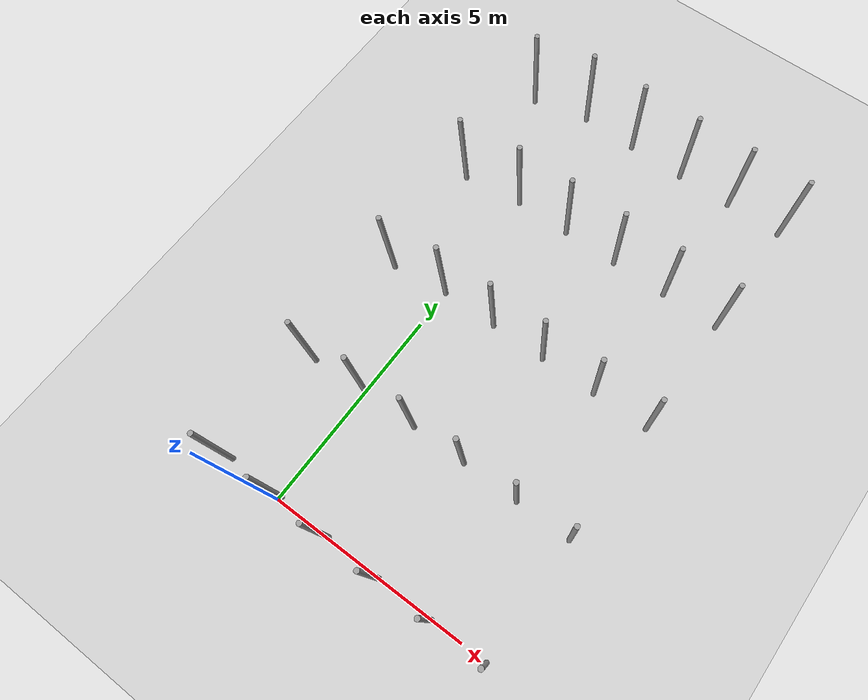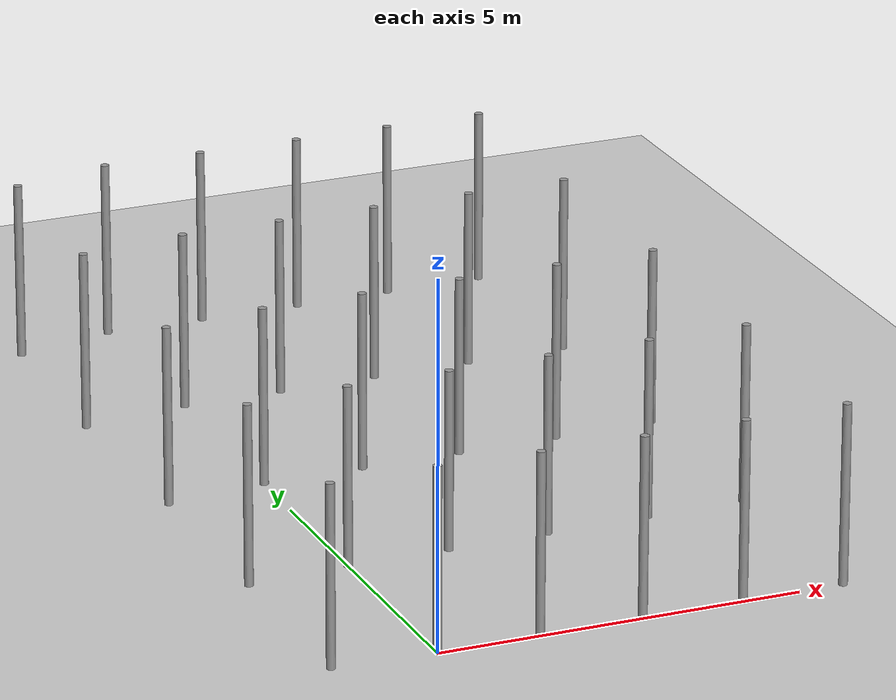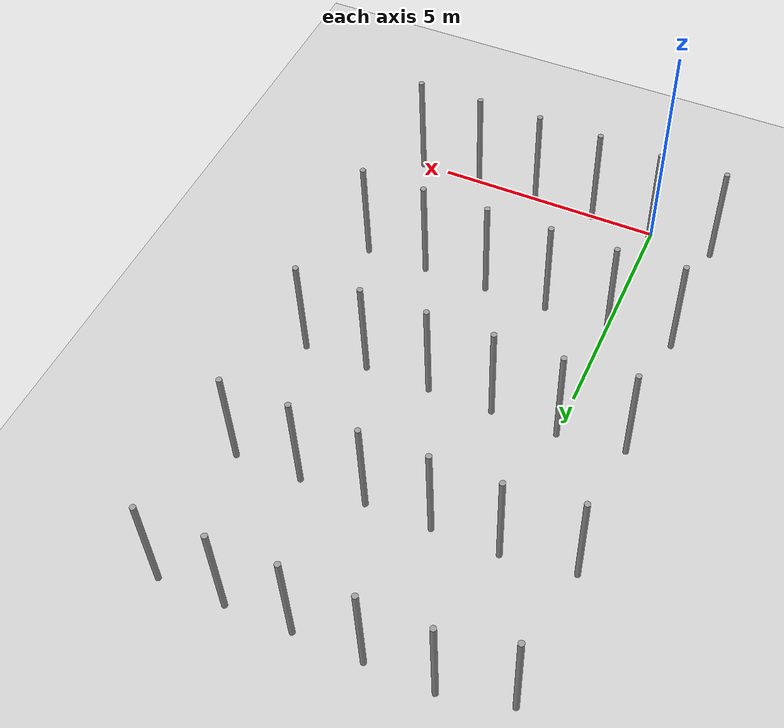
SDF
<sdf version="1.6">
 <world name="default">
  <light name="sun" type="directional">
   <pose>0 0 10 0 -0 0</pose>
   <diffuse>0.8 0.8 0.8 1</diffuse>
   <specular>0.1 0.1 0.1 1</specular>
   <attenuation>
    <range>1000</range>
    <constant>0.9</constant>
    <linear>0.01</linear>
    <quadratic>0.001</quadratic>
   </attenuation>
   <direction>-0.5 0.5 -1</direction>
  </light>
  <model name="ground_plane">
   <static>1</static>
   <link name="link">
    <collision name="collision">
     <geometry><plane><normal>0 0 1</normal><size>100 100</size></plane></geometry>
     <surface><friction><ode><mu>100</mu><mu2>50</mu2></ode></friction></surface>
    </collision>
    <visual name="visual">
     <cast_shadows>0</cast_shadows>
     <geometry><plane><normal>0 0 1</normal><size>100 100</size></plane></geometry>
     <material>
      <script><uri>file://media/materials/scripts/gazebo.material</uri><name>Gazebo/Grey</name></script>
     </material>
    </visual>
   </link>
  </model>
  <gravity>0 0 -9.8</gravity>
  <magnetic_field>6e-06 2.3e-05 -4.2e-05</magnetic_field>
  <atmosphere type="adiabatic"/>
  <physics name="default_physics" default="0" type="ode">
   <max_step_size>0.001</max_step_size>
   <real_time_factor>1</real_time_factor>
   <real_time_update_rate>1000</real_time_update_rate>
  </physics>
  <scene><ambient>0.4 0.4 0.4 1</ambient><background>0.7 0.7 0.7 1</background><shadows>1</shadows></scene>
  <spherical_coordinates>
   <surface_model>EARTH_WGS84</surface_model>
   <latitude_deg>0</latitude_deg>
   <longitude_deg>0</longitude_deg>
   <elevation>0</elevation>
   <heading_deg>0</heading_deg>
  </spherical_coordinates>
  <model name="pole_8">
   <link name="link_0">
    <inertial>
     <mass>0.0364582</mass>
     <inertia>
      <ixx>0.00312124</ixx>
      <ixy>0</ixy>
      <ixz>0</ixz>
      <iyy>0.00312124</iyy>
      <iyz>0</iyz>
      <izz>0.00016615</izz>
     </inertia>
    </inertial>
    <visual name="visual">
     <geometry><cylinder><radius>0.06</radius><length>2.5</length></cylinder></geometry>
     <material>
      <lighting>1</lighting>
      <script><uri>file://media/materials/scripts/gazebo.material</uri><name>Gazebo/Grey</name></script>
      <ambient>0.3 0.3 0.3 1</ambient>
      <diffuse>0.7 0.7 0.7 1</diffuse>
      <specular>0.01 0.01 0.01 1</specular>
      <emissive>0 0 0 1</emissive>
      <shader type="vertex"><normal_map>__default__</normal_map></shader>
     </material>
    </visual>
    <collision name="collision">
     <geometry><cylinder><radius>0.06</radius><length>2.5</length></cylinder></geometry>
     <surface>
      <friction>
       <ode><mu>1</mu><mu2>1</mu2><fdir1>0 0 0</fdir1><slip1>0</slip1><slip2>0</slip2></ode>
       <torsional>
        <coefficient>1</coefficient>
        <patch_radius>0</patch_radius>
        <surface_radius>0</surface_radius>
        <use_patch_radius>1</use_patch_radius>
        <ode><slip>0</slip></ode>
       </torsional>
      </friction>
      <bounce><restitution_coefficient>0</restitution_coefficient><threshold>1e+06</threshold></bounce>
      <contact>
       <collide_without_contact>0</collide_without_contact>
       <collide_without_contact_bitmask>1</collide_without_contact_bitmask>
       <collide_bitmask>1</collide_bitmask>
       <ode>
        <soft_cfm>0</soft_cfm>
        <soft_erp>0.2</soft_erp>
        <kp>1e+13</kp>
        <kd>1</kd>
        <max_vel>0.01</max_vel>
        <min_depth>0</min_depth>
       </ode>
       <bullet>
        <split_impulse>1</split_impulse>
        <split_impulse_penetration_threshold>-0.01</split_impulse_penetration_threshold>
        <soft_cfm>0</soft_cfm>
        <soft_erp>0.2</soft_erp>
        <kp>1e+13</kp>
        <kd>1</kd>
       </bullet>
      </contact>
     </surface>
    </collision>
   </link>
   <static>0</static>
   <pose>1.40879 0.036092 1.24999 1e-06 -3e-06 -0.062165</pose>
  </model>
  <model name="pole_9">
   <link name="link_0">
    <inertial>
     <mass>0.0364582</mass>
     <inertia>
      <ixx>0.00312124</ixx>
      <ixy>0</ixy>
      <ixz>0</ixz>
      <iyy>0.00312124</iyy>
      <iyz>0</iyz>
      <izz>0.00016615</izz>
     </inertia>
    </inertial>
    <visual name="visual">
     <geometry><cylinder><radius>0.06</radius><length>2.5</length></cylinder></geometry>
     <material>
      <lighting>1</lighting>
      <script><uri>file://media/materials/scripts/gazebo.material</uri><name>Gazebo/Grey</name></script>
      <ambient>0.3 0.3 0.3 1</ambient>
      <diffuse>0.7 0.7 0.7 1</diffuse>
      <specular>0.01 0.01 0.01 1</specular>
      <emissive>0 0 0 1</emissive>
      <shader type="vertex"><normal_map>__default__</normal_map></shader>
     </material>
    </visual>
    <collision name="collision">
     <geometry><cylinder><radius>0.06</radius><length>2.5</length></cylinder></geometry>
     <surface>
      <friction>
       <ode><mu>1</mu><mu2>1</mu2><fdir1>0 0 0</fdir1><slip1>0</slip1><slip2>0</slip2></ode>
       <torsional>
        <coefficient>1</coefficient>
        <patch_radius>0</patch_radius>
        <surface_radius>0</surface_radius>
        <use_patch_radius>1</use_patch_radius>
        <ode><slip>0</slip></ode>
       </torsional>
      </friction>
      <bounce><restitution_coefficient>0</restitution_coefficient><threshold>1e+06</threshold></bounce>
      <contact>
       <collide_without_contact>0</collide_without_contact>
       <collide_without_contact_bitmask>1</collide_without_contact_bitmask>
       <collide_bitmask>1</collide_bitmask>
       <ode>
        <soft_cfm>0</soft_cfm>
        <soft_erp>0.2</soft_erp>
        <kp>1e+13</kp>
        <kd>1</kd>
        <max_vel>0.01</max_vel>
        <min_depth>0</min_depth>
       </ode>
       <bullet>
        <split_impulse>1</split_impulse>
        <split_impulse_penetration_threshold>-0.01</split_impulse_penetration_threshold>
        <soft_cfm>0</soft_cfm>
        <soft_erp>0.2</soft_erp>
        <kp>1e+13</kp>
        <kd>1</kd>
       </bullet>
      </contact>
     </surface>
    </collision>
   </link>
   <static>0</static>
   <pose>2.80864 0.005801 1.25 -1e-06 1e-06 -0.08446</pose>
  </model>
  <model name="pole_10">
   <link name="link_0">
    <inertial>
     <mass>0.0364582</mass>
     <inertia>
      <ixx>0.00312124</ixx>
      <ixy>0</ixy>
      <ixz>0</ixz>
      <iyy>0.00312124</iyy>
      <iyz>0</iyz>
      <izz>0.00016615</izz>
     </inertia>
    </inertial>
    <visual name="visual">
     <geometry><cylinder><radius>0.06</radius><length>2.5</length></cylinder></geometry>
     <material>
      <lighting>1</lighting>
      <script><uri>file://media/materials/scripts/gazebo.material</uri><name>Gazebo/Grey</name></script>
      <ambient>0.3 0.3 0.3 1</ambient>
      <diffuse>0.7 0.7 0.7 1</diffuse>
      <specular>0.01 0.01 0.01 1</specular>
      <emissive>0 0 0 1</emissive>
      <shader type="vertex"><normal_map>__default__</normal_map></shader>
     </material>
    </visual>
    <collision name="collision">
     <geometry><cylinder><radius>0.06</radius><length>2.5</length></cylinder></geometry>
     <surface>
      <friction>
       <ode><mu>1</mu><mu2>1</mu2><fdir1>0 0 0</fdir1><slip1>0</slip1><slip2>0</slip2></ode>
       <torsional>
        <coefficient>1</coefficient>
        <patch_radius>0</patch_radius>
        <surface_radius>0</surface_radius>
        <use_patch_radius>1</use_patch_radius>
        <ode><slip>0</slip></ode>
       </torsional>
      </friction>
      <bounce><restitution_coefficient>0</restitution_coefficient><threshold>1e+06</threshold></bounce>
      <contact>
       <collide_without_contact>0</collide_without_contact>
       <collide_without_contact_bitmask>1</collide_without_contact_bitmask>
       <collide_bitmask>1</collide_bitmask>
       <ode>
        <soft_cfm>0</soft_cfm>
        <soft_erp>0.2</soft_erp>
        <kp>1e+13</kp>
        <kd>1</kd>
        <max_vel>0.01</max_vel>
        <min_depth>0</min_depth>
       </ode>
       <bullet>
        <split_impulse>1</split_impulse>
        <split_impulse_penetration_threshold>-0.01</split_impulse_penetration_threshold>
        <soft_cfm>0</soft_cfm>
        <soft_erp>0.2</soft_erp>
        <kp>1e+13</kp>
        <kd>1</kd>
       </bullet>
      </contact>
     </surface>
    </collision>
   </link>
   <static>0</static>
   <pose>4.20447 0.005369 1.25 -0 -1e-06 -0.061855</pose>
  </model>
  <model name="pole_11">
   <link name="link_0">
    <inertial>
     <mass>0.0364582</mass>
     <inertia>
      <ixx>0.00312124</ixx>
      <ixy>0</ixy>
      <ixz>0</ixz>
      <iyy>0.00312124</iyy>
      <iyz>0</iyz>
      <izz>0.00016615</izz>
     </inertia>
    </inertial>
    <visual name="visual">
     <geometry><cylinder><radius>0.06</radius><length>2.5</length></cylinder></geometry>
     <material>
      <lighting>1</lighting>
      <script><uri>file://media/materials/scripts/gazebo.material</uri><name>Gazebo/Grey</name></script>
      <ambient>0.3 0.3 0.3 1</ambient>
      <diffuse>0.7 0.7 0.7 1</diffuse>
      <specular>0.01 0.01 0.01 1</specular>
      <emissive>0 0 0 1</emissive>
      <shader type="vertex"><normal_map>__default__</normal_map></shader>
     </material>
    </visual>
    <collision name="collision">
     <geometry><cylinder><radius>0.06</radius><length>2.5</length></cylinder></geometry>
     <surface>
      <friction>
       <ode><mu>1</mu><mu2>1</mu2><fdir1>0 0 0</fdir1><slip1>0</slip1><slip2>0</slip2></ode>
       <torsional>
        <coefficient>1</coefficient>
        <patch_radius>0</patch_radius>
        <surface_radius>0</surface_radius>
        <use_patch_radius>1</use_patch_radius>
        <ode><slip>0</slip></ode>
       </torsional>
      </friction>
      <bounce><restitution_coefficient>0</restitution_coefficient><threshold>1e+06</threshold></bounce>
      <contact>
       <collide_without_contact>0</collide_without_contact>
       <collide_without_contact_bitmask>1</collide_without_contact_bitmask>
       <collide_bitmask>1</collide_bitmask>
       <ode>
        <soft_cfm>0</soft_cfm>
        <soft_erp>0.2</soft_erp>
        <kp>1e+13</kp>
        <kd>1</kd>
        <max_vel>0.01</max_vel>
        <min_depth>0</min_depth>
       </ode>
       <bullet>
        <split_impulse>1</split_impulse>
        <split_impulse_penetration_threshold>-0.01</split_impulse_penetration_threshold>
        <soft_cfm>0</soft_cfm>
        <soft_erp>0.2</soft_erp>
        <kp>1e+13</kp>
        <kd>1</kd>
       </bullet>
      </contact>
     </surface>
    </collision>
   </link>
   <static>0</static>
   <pose>5.61686 0.005453 1.24999 0 0 -0.070687</pose>
  </model>
  <model name="pole_11_clone">
   <link name="link_0">
    <inertial>
     <mass>0.0364582</mass>
     <inertia>
      <ixx>0.00312124</ixx>
      <ixy>0</ixy>
      <ixz>0</ixz>
      <iyy>0.00312124</iyy>
      <iyz>0</iyz>
      <izz>0.00016615</izz>
     </inertia>
    </inertial>
    <visual name="visual">
     <geometry><cylinder><radius>0.06</radius><length>2.5</length></cylinder></geometry>
     <material>
      <lighting>1</lighting>
      <script><uri>file://media/materials/scripts/gazebo.material</uri><name>Gazebo/Grey</name></script>
      <ambient>0.3 0.3 0.3 1</ambient>
      <diffuse>0.7 0.7 0.7 1</diffuse>
      <specular>0.01 0.01 0.01 1</specular>
      <emissive>0 0 0 1</emissive>
      <shader type="vertex"><normal_map>__default__</normal_map></shader>
     </material>
    </visual>
    <collision name="collision">
     <geometry><cylinder><radius>0.06</radius><length>2.5</length></cylinder></geometry>
     <surface>
      <friction>
       <ode><mu>1</mu><mu2>1</mu2><fdir1>0 0 0</fdir1><slip1>0</slip1><slip2>0</slip2></ode>
       <torsional>
        <coefficient>1</coefficient>
        <patch_radius>0</patch_radius>
        <surface_radius>0</surface_radius>
        <use_patch_radius>1</use_patch_radius>
        <ode><slip>0</slip></ode>
       </torsional>
      </friction>
      <bounce><restitution_coefficient>0</restitution_coefficient><threshold>1e+06</threshold></bounce>
      <contact>
       <collide_without_contact>0</collide_without_contact>
       <collide_without_contact_bitmask>1</collide_without_contact_bitmask>
       <collide_bitmask>1</collide_bitmask>
       <ode>
        <soft_cfm>0</soft_cfm>
        <soft_erp>0.2</soft_erp>
        <kp>1e+13</kp>
        <kd>1</kd>
        <max_vel>0.01</max_vel>
        <min_depth>0</min_depth>
       </ode>
       <bullet>
        <split_impulse>1</split_impulse>
        <split_impulse_penetration_threshold>-0.01</split_impulse_penetration_threshold>
        <soft_cfm>0</soft_cfm>
        <soft_erp>0.2</soft_erp>
        <kp>1e+13</kp>
        <kd>1</kd>
       </bullet>
      </contact>
     </surface>
    </collision>
   </link>
   <static>0</static>
   <pose>0.001297 2.98765 1.25 0 1e-06 -0.073133</pose>
  </model>
  <model name="pole">
   <link name="link_0">
    <inertial>
     <mass>0.0364582</mass>
     <inertia>
      <ixx>0.00312124</ixx>
      <ixy>0</ixy>
      <ixz>0</ixz>
      <iyy>0.00312124</iyy>
      <iyz>0</iyz>
      <izz>0.00016615</izz>
     </inertia>
    </inertial>
    <visual name="visual">
     <geometry><cylinder><radius>0.06</radius><length>2.5</length></cylinder></geometry>
     <material>
      <lighting>1</lighting>
      <script><uri>file://media/materials/scripts/gazebo.material</uri><name>Gazebo/Grey</name></script>
      <ambient>0.3 0.3 0.3 1</ambient>
      <diffuse>0.7 0.7 0.7 1</diffuse>
      <specular>0.01 0.01 0.01 1</specular>
      <emissive>0 0 0 1</emissive>
      <shader type="vertex"><normal_map>__default__</normal_map></shader>
     </material>
    </visual>
    <collision name="collision">
     <geometry><cylinder><radius>0.06</radius><length>2.5</length></cylinder></geometry>
     <surface>
      <friction>
       <ode><mu>1</mu><mu2>1</mu2><fdir1>0 0 0</fdir1><slip1>0</slip1><slip2>0</slip2></ode>
       <torsional>
        <coefficient>1</coefficient>
        <patch_radius>0</patch_radius>
        <surface_radius>0</surface_radius>
        <use_patch_radius>1</use_patch_radius>
        <ode><slip>0</slip></ode>
       </torsional>
      </friction>
      <bounce><restitution_coefficient>0</restitution_coefficient><threshold>1e+06</threshold></bounce>
      <contact>
       <collide_without_contact>0</collide_without_contact>
       <collide_without_contact_bitmask>1</collide_without_contact_bitmask>
       <collide_bitmask>1</collide_bitmask>
       <ode>
        <soft_cfm>0</soft_cfm>
        <soft_erp>0.2</soft_erp>
        <kp>1e+13</kp>
        <kd>1</kd>
        <max_vel>0.01</max_vel>
        <min_depth>0</min_depth>
       </ode>
       <bullet>
        <split_impulse>1</split_impulse>
        <split_impulse_penetration_threshold>-0.01</split_impulse_penetration_threshold>
        <soft_cfm>0</soft_cfm>
        <soft_erp>0.2</soft_erp>
        <kp>1e+13</kp>
        <kd>1</kd>
       </bullet>
      </contact>
     </surface>
    </collision>
   </link>
   <static>0</static>
   <pose>0.00729 5.96546 1.24999 0 1e-06 -0.061917</pose>
  </model>
  <model name="pole_0">
   <link name="link_0">
    <inertial>
     <mass>0.0364582</mass>
     <inertia>
      <ixx>0.00312124</ixx>
      <ixy>0</ixy>
      <ixz>0</ixz>
      <iyy>0.00312124</iyy>
      <iyz>0</iyz>
      <izz>0.00016615</izz>
     </inertia>
    </inertial>
    <visual name="visual">
     <geometry><cylinder><radius>0.06</radius><length>2.5</length></cylinder></geometry>
     <material>
      <lighting>1</lighting>
      <script><uri>file://media/materials/scripts/gazebo.material</uri><name>Gazebo/Grey</name></script>
      <ambient>0.3 0.3 0.3 1</ambient>
      <diffuse>0.7 0.7 0.7 1</diffuse>
      <specular>0.01 0.01 0.01 1</specular>
      <emissive>0 0 0 1</emissive>
      <shader type="vertex"><normal_map>__default__</normal_map></shader>
     </material>
    </visual>
    <collision name="collision">
     <geometry><cylinder><radius>0.06</radius><length>2.5</length></cylinder></geometry>
     <surface>
      <friction>
       <ode><mu>1</mu><mu2>1</mu2><fdir1>0 0 0</fdir1><slip1>0</slip1><slip2>0</slip2></ode>
       <torsional>
        <coefficient>1</coefficient>
        <patch_radius>0</patch_radius>
        <surface_radius>0</surface_radius>
        <use_patch_radius>1</use_patch_radius>
        <ode><slip>0</slip></ode>
       </torsional>
      </friction>
      <bounce><restitution_coefficient>0</restitution_coefficient><threshold>1e+06</threshold></bounce>
      <contact>
       <collide_without_contact>0</collide_without_contact>
       <collide_without_contact_bitmask>1</collide_without_contact_bitmask>
       <collide_bitmask>1</collide_bitmask>
       <ode>
        <soft_cfm>0</soft_cfm>
        <soft_erp>0.2</soft_erp>
        <kp>1e+13</kp>
        <kd>1</kd>
        <max_vel>0.01</max_vel>
        <min_depth>0</min_depth>
       </ode>
       <bullet>
        <split_impulse>1</split_impulse>
        <split_impulse_penetration_threshold>-0.01</split_impulse_penetration_threshold>
        <soft_cfm>0</soft_cfm>
        <soft_erp>0.2</soft_erp>
        <kp>1e+13</kp>
        <kd>1</kd>
       </bullet>
      </contact>
     </surface>
    </collision>
   </link>
   <static>0</static>
   <pose>0.014052 8.94503 1.24999 -1e-06 1e-06 -0.061083</pose>
  </model>
  <model name="pole_1">
   <link name="link_0">
    <inertial>
     <mass>0.0364582</mass>
     <inertia>
      <ixx>0.00312124</ixx>
      <ixy>0</ixy>
      <ixz>0</ixz>
      <iyy>0.00312124</iyy>
      <iyz>0</iyz>
      <izz>0.00016615</izz>
     </inertia>
    </inertial>
    <visual name="visual">
     <geometry><cylinder><radius>0.06</radius><length>2.5</length></cylinder></geometry>
     <material>
      <lighting>1</lighting>
      <script><uri>file://media/materials/scripts/gazebo.material</uri><name>Gazebo/Grey</name></script>
      <ambient>0.3 0.3 0.3 1</ambient>
      <diffuse>0.7 0.7 0.7 1</diffuse>
      <specular>0.01 0.01 0.01 1</specular>
      <emissive>0 0 0 1</emissive>
      <shader type="vertex"><normal_map>__default__</normal_map></shader>
     </material>
    </visual>
    <collision name="collision">
     <geometry><cylinder><radius>0.06</radius><length>2.5</length></cylinder></geometry>
     <surface>
      <friction>
       <ode><mu>1</mu><mu2>1</mu2><fdir1>0 0 0</fdir1><slip1>0</slip1><slip2>0</slip2></ode>
       <torsional>
        <coefficient>1</coefficient>
        <patch_radius>0</patch_radius>
        <surface_radius>0</surface_radius>
        <use_patch_radius>1</use_patch_radius>
        <ode><slip>0</slip></ode>
       </torsional>
      </friction>
      <bounce><restitution_coefficient>0</restitution_coefficient><threshold>1e+06</threshold></bounce>
      <contact>
       <collide_without_contact>0</collide_without_contact>
       <collide_without_contact_bitmask>1</collide_without_contact_bitmask>
       <collide_bitmask>1</collide_bitmask>
       <ode>
        <soft_cfm>0</soft_cfm>
        <soft_erp>0.2</soft_erp>
        <kp>1e+13</kp>
        <kd>1</kd>
        <max_vel>0.01</max_vel>
        <min_depth>0</min_depth>
       </ode>
       <bullet>
        <split_impulse>1</split_impulse>
        <split_impulse_penetration_threshold>-0.01</split_impulse_penetration_threshold>
        <soft_cfm>0</soft_cfm>
        <soft_erp>0.2</soft_erp>
        <kp>1e+13</kp>
        <kd>1</kd>
       </bullet>
      </contact>
     </surface>
    </collision>
   </link>
   <static>0</static>
   <pose>-0.007502 11.9252 1.24999 -1e-06 1e-06 -0.066059</pose>
  </model>
  <model name="pole_2">
   <link name="link_0">
    <inertial>
     <mass>0.0364582</mass>
     <inertia>
      <ixx>0.00312124</ixx>
      <ixy>0</ixy>
      <ixz>0</ixz>
      <iyy>0.00312124</iyy>
      <iyz>0</iyz>
      <izz>0.00016615</izz>
     </inertia>
    </inertial>
    <visual name="visual">
     <geometry><cylinder><radius>0.06</radius><length>2.5</length></cylinder></geometry>
     <material>
      <lighting>1</lighting>
      <script><uri>file://media/materials/scripts/gazebo.material</uri><name>Gazebo/Grey</name></script>
      <ambient>0.3 0.3 0.3 1</ambient>
      <diffuse>0.7 0.7 0.7 1</diffuse>
      <specular>0.01 0.01 0.01 1</specular>
      <emissive>0 0 0 1</emissive>
      <shader type="vertex"><normal_map>__default__</normal_map></shader>
     </material>
    </visual>
    <collision name="collision">
     <geometry><cylinder><radius>0.06</radius><length>2.5</length></cylinder></geometry>
     <surface>
      <friction>
       <ode><mu>1</mu><mu2>1</mu2><fdir1>0 0 0</fdir1><slip1>0</slip1><slip2>0</slip2></ode>
       <torsional>
        <coefficient>1</coefficient>
        <patch_radius>0</patch_radius>
        <surface_radius>0</surface_radius>
        <use_patch_radius>1</use_patch_radius>
        <ode><slip>0</slip></ode>
       </torsional>
      </friction>
      <bounce><restitution_coefficient>0</restitution_coefficient><threshold>1e+06</threshold></bounce>
      <contact>
       <collide_without_contact>0</collide_without_contact>
       <collide_without_contact_bitmask>1</collide_without_contact_bitmask>
       <collide_bitmask>1</collide_bitmask>
       <ode>
        <soft_cfm>0</soft_cfm>
        <soft_erp>0.2</soft_erp>
        <kp>1e+13</kp>
        <kd>1</kd>
        <max_vel>0.01</max_vel>
        <min_depth>0</min_depth>
       </ode>
       <bullet>
        <split_impulse>1</split_impulse>
        <split_impulse_penetration_threshold>-0.01</split_impulse_penetration_threshold>
        <soft_cfm>0</soft_cfm>
        <soft_erp>0.2</soft_erp>
        <kp>1e+13</kp>
        <kd>1</kd>
       </bullet>
      </contact>
     </surface>
    </collision>
   </link>
   <static>0</static>
   <pose>0.034803 0.098134 1.25 0 2e-06 0.003122</pose>
  </model>
  <model name="pole_3">
   <link name="link_0">
    <inertial>
     <mass>0.0364582</mass>
     <inertia>
      <ixx>0.00312124</ixx>
      <ixy>0</ixy>
      <ixz>0</ixz>
      <iyy>0.00312124</iyy>
      <iyz>0</iyz>
      <izz>0.00016615</izz>
     </inertia>
    </inertial>
    <visual name="visual">
     <geometry><cylinder><radius>0.06</radius><length>2.5</length></cylinder></geometry>
     <material>
      <lighting>1</lighting>
      <script><uri>file://media/materials/scripts/gazebo.material</uri><name>Gazebo/Grey</name></script>
      <ambient>0.3 0.3 0.3 1</ambient>
      <diffuse>0.7 0.7 0.7 1</diffuse>
      <specular>0.01 0.01 0.01 1</specular>
      <emissive>0 0 0 1</emissive>
      <shader type="vertex"><normal_map>__default__</normal_map></shader>
     </material>
    </visual>
    <collision name="collision">
     <geometry><cylinder><radius>0.06</radius><length>2.5</length></cylinder></geometry>
     <surface>
      <friction>
       <ode><mu>1</mu><mu2>1</mu2><fdir1>0 0 0</fdir1><slip1>0</slip1><slip2>0</slip2></ode>
       <torsional>
        <coefficient>1</coefficient>
        <patch_radius>0</patch_radius>
        <surface_radius>0</surface_radius>
        <use_patch_radius>1</use_patch_radius>
        <ode><slip>0</slip></ode>
       </torsional>
      </friction>
      <bounce><restitution_coefficient>0</restitution_coefficient><threshold>1e+06</threshold></bounce>
      <contact>
       <collide_without_contact>0</collide_without_contact>
       <collide_without_contact_bitmask>1</collide_without_contact_bitmask>
       <collide_bitmask>1</collide_bitmask>
       <ode>
        <soft_cfm>0</soft_cfm>
        <soft_erp>0.2</soft_erp>
        <kp>1e+13</kp>
        <kd>1</kd>
        <max_vel>0.01</max_vel>
        <min_depth>0</min_depth>
       </ode>
       <bullet>
        <split_impulse>1</split_impulse>
        <split_impulse_penetration_threshold>-0.01</split_impulse_penetration_threshold>
        <soft_cfm>0</soft_cfm>
        <soft_erp>0.2</soft_erp>
        <kp>1e+13</kp>
        <kd>1</kd>
       </bullet>
      </contact>
     </surface>
    </collision>
   </link>
   <static>0</static>
   <pose>1.40528 2.98526 1.25 -1e-06 -0 -0.058774</pose>
  </model>
  <model name="pole_5">
   <link name="link_0">
    <inertial>
     <mass>0.0364582</mass>
     <inertia>
      <ixx>0.00312124</ixx>
      <ixy>0</ixy>
      <ixz>0</ixz>
      <iyy>0.00312124</iyy>
      <iyz>0</iyz>
      <izz>0.00016615</izz>
     </inertia>
    </inertial>
    <visual name="visual">
     <geometry><cylinder><radius>0.06</radius><length>2.5</length></cylinder></geometry>
     <material>
      <lighting>1</lighting>
      <script><uri>file://media/materials/scripts/gazebo.material</uri><name>Gazebo/Grey</name></script>
      <ambient>0.3 0.3 0.3 1</ambient>
      <diffuse>0.7 0.7 0.7 1</diffuse>
      <specular>0.01 0.01 0.01 1</specular>
      <emissive>0 0 0 1</emissive>
      <shader type="vertex"><normal_map>__default__</normal_map></shader>
     </material>
    </visual>
    <collision name="collision">
     <geometry><cylinder><radius>0.06</radius><length>2.5</length></cylinder></geometry>
     <surface>
      <friction>
       <ode><mu>1</mu><mu2>1</mu2><fdir1>0 0 0</fdir1><slip1>0</slip1><slip2>0</slip2></ode>
       <torsional>
        <coefficient>1</coefficient>
        <patch_radius>0</patch_radius>
        <surface_radius>0</surface_radius>
        <use_patch_radius>1</use_patch_radius>
        <ode><slip>0</slip></ode>
       </torsional>
      </friction>
      <bounce><restitution_coefficient>0</restitution_coefficient><threshold>1e+06</threshold></bounce>
      <contact>
       <collide_without_contact>0</collide_without_contact>
       <collide_without_contact_bitmask>1</collide_without_contact_bitmask>
       <collide_bitmask>1</collide_bitmask>
       <ode>
        <soft_cfm>0</soft_cfm>
        <soft_erp>0.2</soft_erp>
        <kp>1e+13</kp>
        <kd>1</kd>
        <max_vel>0.01</max_vel>
        <min_depth>0</min_depth>
       </ode>
       <bullet>
        <split_impulse>1</split_impulse>
        <split_impulse_penetration_threshold>-0.01</split_impulse_penetration_threshold>
        <soft_cfm>0</soft_cfm>
        <soft_erp>0.2</soft_erp>
        <kp>1e+13</kp>
        <kd>1</kd>
       </bullet>
      </contact>
     </surface>
    </collision>
   </link>
   <static>0</static>
   <pose>2.79633 2.98472 1.24999 0 -1e-06 -0.053826</pose>
  </model>
  <model name="pole_6">
   <link name="link_0">
    <inertial>
     <mass>0.0364582</mass>
     <inertia>
      <ixx>0.00312124</ixx>
      <ixy>0</ixy>
      <ixz>0</ixz>
      <iyy>0.00312124</iyy>
      <iyz>0</iyz>
      <izz>0.00016615</izz>
     </inertia>
    </inertial>
    <visual name="visual">
     <geometry><cylinder><radius>0.06</radius><length>2.5</length></cylinder></geometry>
     <material>
      <lighting>1</lighting>
      <script><uri>file://media/materials/scripts/gazebo.material</uri><name>Gazebo/Grey</name></script>
      <ambient>0.3 0.3 0.3 1</ambient>
      <diffuse>0.7 0.7 0.7 1</diffuse>
      <specular>0.01 0.01 0.01 1</specular>
      <emissive>0 0 0 1</emissive>
      <shader type="vertex"><normal_map>__default__</normal_map></shader>
     </material>
    </visual>
    <collision name="collision">
     <geometry><cylinder><radius>0.06</radius><length>2.5</length></cylinder></geometry>
     <surface>
      <friction>
       <ode><mu>1</mu><mu2>1</mu2><fdir1>0 0 0</fdir1><slip1>0</slip1><slip2>0</slip2></ode>
       <torsional>
        <coefficient>1</coefficient>
        <patch_radius>0</patch_radius>
        <surface_radius>0</surface_radius>
        <use_patch_radius>1</use_patch_radius>
        <ode><slip>0</slip></ode>
       </torsional>
      </friction>
      <bounce><restitution_coefficient>0</restitution_coefficient><threshold>1e+06</threshold></bounce>
      <contact>
       <collide_without_contact>0</collide_without_contact>
       <collide_without_contact_bitmask>1</collide_without_contact_bitmask>
       <collide_bitmask>1</collide_bitmask>
       <ode>
        <soft_cfm>0</soft_cfm>
        <soft_erp>0.2</soft_erp>
        <kp>1e+13</kp>
        <kd>1</kd>
        <max_vel>0.01</max_vel>
        <min_depth>0</min_depth>
       </ode>
       <bullet>
        <split_impulse>1</split_impulse>
        <split_impulse_penetration_threshold>-0.01</split_impulse_penetration_threshold>
        <soft_cfm>0</soft_cfm>
        <soft_erp>0.2</soft_erp>
        <kp>1e+13</kp>
        <kd>1</kd>
       </bullet>
      </contact>
     </surface>
    </collision>
   </link>
   <static>0</static>
   <pose>4.22295 2.98489 1.25 -0 1e-06 -0.055061</pose>
  </model>
  <model name="pole_7">
   <link name="link_0">
    <inertial>
     <mass>0.0364582</mass>
     <inertia>
      <ixx>0.00312124</ixx>
      <ixy>0</ixy>
      <ixz>0</ixz>
      <iyy>0.00312124</iyy>
      <iyz>0</iyz>
      <izz>0.00016615</izz>
     </inertia>
    </inertial>
    <visual name="visual">
     <geometry><cylinder><radius>0.06</radius><length>2.5</length></cylinder></geometry>
     <material>
      <lighting>1</lighting>
      <script><uri>file://media/materials/scripts/gazebo.material</uri><name>Gazebo/Grey</name></script>
      <ambient>0.3 0.3 0.3 1</ambient>
      <diffuse>0.7 0.7 0.7 1</diffuse>
      <specular>0.01 0.01 0.01 1</specular>
      <emissive>0 0 0 1</emissive>
      <shader type="vertex"><normal_map>__default__</normal_map></shader>
     </material>
    </visual>
    <collision name="collision">
     <geometry><cylinder><radius>0.06</radius><length>2.5</length></cylinder></geometry>
     <surface>
      <friction>
       <ode><mu>1</mu><mu2>1</mu2><fdir1>0 0 0</fdir1><slip1>0</slip1><slip2>0</slip2></ode>
       <torsional>
        <coefficient>1</coefficient>
        <patch_radius>0</patch_radius>
        <surface_radius>0</surface_radius>
        <use_patch_radius>1</use_patch_radius>
        <ode><slip>0</slip></ode>
       </torsional>
      </friction>
      <bounce><restitution_coefficient>0</restitution_coefficient><threshold>1e+06</threshold></bounce>
      <contact>
       <collide_without_contact>0</collide_without_contact>
       <collide_without_contact_bitmask>1</collide_without_contact_bitmask>
       <collide_bitmask>1</collide_bitmask>
       <ode>
        <soft_cfm>0</soft_cfm>
        <soft_erp>0.2</soft_erp>
        <kp>1e+13</kp>
        <kd>1</kd>
        <max_vel>0.01</max_vel>
        <min_depth>0</min_depth>
       </ode>
       <bullet>
        <split_impulse>1</split_impulse>
        <split_impulse_penetration_threshold>-0.01</split_impulse_penetration_threshold>
        <soft_cfm>0</soft_cfm>
        <soft_erp>0.2</soft_erp>
        <kp>1e+13</kp>
        <kd>1</kd>
       </bullet>
      </contact>
     </surface>
    </collision>
   </link>
   <static>0</static>
   <pose>5.60791 2.98497 1.24999 0 0 -0.056686</pose>
  </model>
  <model name="pole_12">
   <link name="link_0">
    <inertial>
     <mass>0.0364582</mass>
     <inertia>
      <ixx>0.00312124</ixx>
      <ixy>0</ixy>
      <ixz>0</ixz>
      <iyy>0.00312124</iyy>
      <iyz>0</iyz>
      <izz>0.00016615</izz>
     </inertia>
    </inertial>
    <visual name="visual">
     <geometry><cylinder><radius>0.06</radius><length>2.5</length></cylinder></geometry>
     <material>
      <lighting>1</lighting>
      <script><uri>file://media/materials/scripts/gazebo.material</uri><name>Gazebo/Grey</name></script>
      <ambient>0.3 0.3 0.3 1</ambient>
      <diffuse>0.7 0.7 0.7 1</diffuse>
      <specular>0.01 0.01 0.01 1</specular>
      <emissive>0 0 0 1</emissive>
      <shader type="vertex"><normal_map>__default__</normal_map></shader>
     </material>
    </visual>
    <collision name="collision">
     <geometry><cylinder><radius>0.06</radius><length>2.5</length></cylinder></geometry>
     <surface>
      <friction>
       <ode><mu>1</mu><mu2>1</mu2><fdir1>0 0 0</fdir1><slip1>0</slip1><slip2>0</slip2></ode>
       <torsional>
        <coefficient>1</coefficient>
        <patch_radius>0</patch_radius>
        <surface_radius>0</surface_radius>
        <use_patch_radius>1</use_patch_radius>
        <ode><slip>0</slip></ode>
       </torsional>
      </friction>
      <bounce><restitution_coefficient>0</restitution_coefficient><threshold>1e+06</threshold></bounce>
      <contact>
       <collide_without_contact>0</collide_without_contact>
       <collide_without_contact_bitmask>1</collide_without_contact_bitmask>
       <collide_bitmask>1</collide_bitmask>
       <ode>
        <soft_cfm>0</soft_cfm>
        <soft_erp>0.2</soft_erp>
        <kp>1e+13</kp>
        <kd>1</kd>
        <max_vel>0.01</max_vel>
        <min_depth>0</min_depth>
       </ode>
       <bullet>
        <split_impulse>1</split_impulse>
        <split_impulse_penetration_threshold>-0.01</split_impulse_penetration_threshold>
        <soft_cfm>0</soft_cfm>
        <soft_erp>0.2</soft_erp>
        <kp>1e+13</kp>
        <kd>1</kd>
       </bullet>
      </contact>
     </surface>
    </collision>
   </link>
   <static>0</static>
   <pose>1.41418 5.96502 1.24999 -0 1e-06 -0.0547</pose>
  </model>
  <model name="pole_13">
   <link name="link_0">
    <inertial>
     <mass>0.0364582</mass>
     <inertia>
      <ixx>0.00312124</ixx>
      <ixy>0</ixy>
      <ixz>0</ixz>
      <iyy>0.00312124</iyy>
      <iyz>0</iyz>
      <izz>0.00016615</izz>
     </inertia>
    </inertial>
    <visual name="visual">
     <geometry><cylinder><radius>0.06</radius><length>2.5</length></cylinder></geometry>
     <material>
      <lighting>1</lighting>
      <script><uri>file://media/materials/scripts/gazebo.material</uri><name>Gazebo/Grey</name></script>
      <ambient>0.3 0.3 0.3 1</ambient>
      <diffuse>0.7 0.7 0.7 1</diffuse>
      <specular>0.01 0.01 0.01 1</specular>
      <emissive>0 0 0 1</emissive>
      <shader type="vertex"><normal_map>__default__</normal_map></shader>
     </material>
    </visual>
    <collision name="collision">
     <geometry><cylinder><radius>0.06</radius><length>2.5</length></cylinder></geometry>
     <surface>
      <friction>
       <ode><mu>1</mu><mu2>1</mu2><fdir1>0 0 0</fdir1><slip1>0</slip1><slip2>0</slip2></ode>
       <torsional>
        <coefficient>1</coefficient>
        <patch_radius>0</patch_radius>
        <surface_radius>0</surface_radius>
        <use_patch_radius>1</use_patch_radius>
        <ode><slip>0</slip></ode>
       </torsional>
      </friction>
      <bounce><restitution_coefficient>0</restitution_coefficient><threshold>1e+06</threshold></bounce>
      <contact>
       <collide_without_contact>0</collide_without_contact>
       <collide_without_contact_bitmask>1</collide_without_contact_bitmask>
       <collide_bitmask>1</collide_bitmask>
       <ode>
        <soft_cfm>0</soft_cfm>
        <soft_erp>0.2</soft_erp>
        <kp>1e+13</kp>
        <kd>1</kd>
        <max_vel>0.01</max_vel>
        <min_depth>0</min_depth>
       </ode>
       <bullet>
        <split_impulse>1</split_impulse>
        <split_impulse_penetration_threshold>-0.01</split_impulse_penetration_threshold>
        <soft_cfm>0</soft_cfm>
        <soft_erp>0.2</soft_erp>
        <kp>1e+13</kp>
        <kd>1</kd>
       </bullet>
      </contact>
     </surface>
    </collision>
   </link>
   <static>0</static>
   <pose>2.80861 5.96514 1.25 -1e-06 -1e-06 -0.056191</pose>
  </model>
  <model name="pole_14">
   <link name="link_0">
    <inertial>
     <mass>0.0364582</mass>
     <inertia>
      <ixx>0.00312124</ixx>
      <ixy>0</ixy>
      <ixz>0</ixz>
      <iyy>0.00312124</iyy>
      <iyz>0</iyz>
      <izz>0.00016615</izz>
     </inertia>
    </inertial>
    <visual name="visual">
     <geometry><cylinder><radius>0.06</radius><length>2.5</length></cylinder></geometry>
     <material>
      <lighting>1</lighting>
      <script><uri>file://media/materials/scripts/gazebo.material</uri><name>Gazebo/Grey</name></script>
      <ambient>0.3 0.3 0.3 1</ambient>
      <diffuse>0.7 0.7 0.7 1</diffuse>
      <specular>0.01 0.01 0.01 1</specular>
      <emissive>0 0 0 1</emissive>
      <shader type="vertex"><normal_map>__default__</normal_map></shader>
     </material>
    </visual>
    <collision name="collision">
     <geometry><cylinder><radius>0.06</radius><length>2.5</length></cylinder></geometry>
     <surface>
      <friction>
       <ode><mu>1</mu><mu2>1</mu2><fdir1>0 0 0</fdir1><slip1>0</slip1><slip2>0</slip2></ode>
       <torsional>
        <coefficient>1</coefficient>
        <patch_radius>0</patch_radius>
        <surface_radius>0</surface_radius>
        <use_patch_radius>1</use_patch_radius>
        <ode><slip>0</slip></ode>
       </torsional>
      </friction>
      <bounce><restitution_coefficient>0</restitution_coefficient><threshold>1e+06</threshold></bounce>
      <contact>
       <collide_without_contact>0</collide_without_contact>
       <collide_without_contact_bitmask>1</collide_without_contact_bitmask>
       <collide_bitmask>1</collide_bitmask>
       <ode>
        <soft_cfm>0</soft_cfm>
        <soft_erp>0.2</soft_erp>
        <kp>1e+13</kp>
        <kd>1</kd>
        <max_vel>0.01</max_vel>
        <min_depth>0</min_depth>
       </ode>
       <bullet>
        <split_impulse>1</split_impulse>
        <split_impulse_penetration_threshold>-0.01</split_impulse_penetration_threshold>
        <soft_cfm>0</soft_cfm>
        <soft_erp>0.2</soft_erp>
        <kp>1e+13</kp>
        <kd>1</kd>
       </bullet>
      </contact>
     </surface>
    </collision>
   </link>
   <static>0</static>
   <pose>4.22007 5.96473 1.24999 -1e-06 1e-06 -0.05686</pose>
  </model>
  <model name="pole_15">
   <link name="link_0">
    <inertial>
     <mass>0.0364582</mass>
     <inertia>
      <ixx>0.00312124</ixx>
      <ixy>0</ixy>
      <ixz>0</ixz>
      <iyy>0.00312124</iyy>
      <iyz>0</iyz>
      <izz>0.00016615</izz>
     </inertia>
    </inertial>
    <visual name="visual">
     <geometry><cylinder><radius>0.06</radius><length>2.5</length></cylinder></geometry>
     <material>
      <lighting>1</lighting>
      <script><uri>file://media/materials/scripts/gazebo.material</uri><name>Gazebo/Grey</name></script>
      <ambient>0.3 0.3 0.3 1</ambient>
      <diffuse>0.7 0.7 0.7 1</diffuse>
      <specular>0.01 0.01 0.01 1</specular>
      <emissive>0 0 0 1</emissive>
      <shader type="vertex"><normal_map>__default__</normal_map></shader>
     </material>
    </visual>
    <collision name="collision">
     <geometry><cylinder><radius>0.06</radius><length>2.5</length></cylinder></geometry>
     <surface>
      <friction>
       <ode><mu>1</mu><mu2>1</mu2><fdir1>0 0 0</fdir1><slip1>0</slip1><slip2>0</slip2></ode>
       <torsional>
        <coefficient>1</coefficient>
        <patch_radius>0</patch_radius>
        <surface_radius>0</surface_radius>
        <use_patch_radius>1</use_patch_radius>
        <ode><slip>0</slip></ode>
       </torsional>
      </friction>
      <bounce><restitution_coefficient>0</restitution_coefficient><threshold>1e+06</threshold></bounce>
      <contact>
       <collide_without_contact>0</collide_without_contact>
       <collide_without_contact_bitmask>1</collide_without_contact_bitmask>
       <collide_bitmask>1</collide_bitmask>
       <ode>
        <soft_cfm>0</soft_cfm>
        <soft_erp>0.2</soft_erp>
        <kp>1e+13</kp>
        <kd>1</kd>
        <max_vel>0.01</max_vel>
        <min_depth>0</min_depth>
       </ode>
       <bullet>
        <split_impulse>1</split_impulse>
        <split_impulse_penetration_threshold>-0.01</split_impulse_penetration_threshold>
        <soft_cfm>0</soft_cfm>
        <soft_erp>0.2</soft_erp>
        <kp>1e+13</kp>
        <kd>1</kd>
       </bullet>
      </contact>
     </surface>
    </collision>
   </link>
   <static>0</static>
   <pose>5.62404 5.96502 1.24999 0 2e-06 -0.052758</pose>
  </model>
  <model name="pole_16">
   <link name="link_0">
    <inertial>
     <mass>0.0364582</mass>
     <inertia>
      <ixx>0.00312124</ixx>
      <ixy>0</ixy>
      <ixz>0</ixz>
      <iyy>0.00312124</iyy>
      <iyz>0</iyz>
      <izz>0.00016615</izz>
     </inertia>
    </inertial>
    <visual name="visual">
     <geometry><cylinder><radius>0.06</radius><length>2.5</length></cylinder></geometry>
     <material>
      <lighting>1</lighting>
      <script><uri>file://media/materials/scripts/gazebo.material</uri><name>Gazebo/Grey</name></script>
      <ambient>0.3 0.3 0.3 1</ambient>
      <diffuse>0.7 0.7 0.7 1</diffuse>
      <specular>0.01 0.01 0.01 1</specular>
      <emissive>0 0 0 1</emissive>
      <shader type="vertex"><normal_map>__default__</normal_map></shader>
     </material>
    </visual>
    <collision name="collision">
     <geometry><cylinder><radius>0.06</radius><length>2.5</length></cylinder></geometry>
     <surface>
      <friction>
       <ode><mu>1</mu><mu2>1</mu2><fdir1>0 0 0</fdir1><slip1>0</slip1><slip2>0</slip2></ode>
       <torsional>
        <coefficient>1</coefficient>
        <patch_radius>0</patch_radius>
        <surface_radius>0</surface_radius>
        <use_patch_radius>1</use_patch_radius>
        <ode><slip>0</slip></ode>
       </torsional>
      </friction>
      <bounce><restitution_coefficient>0</restitution_coefficient><threshold>1e+06</threshold></bounce>
      <contact>
       <collide_without_contact>0</collide_without_contact>
       <collide_without_contact_bitmask>1</collide_without_contact_bitmask>
       <collide_bitmask>1</collide_bitmask>
       <ode>
        <soft_cfm>0</soft_cfm>
        <soft_erp>0.2</soft_erp>
        <kp>1e+13</kp>
        <kd>1</kd>
        <max_vel>0.01</max_vel>
        <min_depth>0</min_depth>
       </ode>
       <bullet>
        <split_impulse>1</split_impulse>
        <split_impulse_penetration_threshold>-0.01</split_impulse_penetration_threshold>
        <soft_cfm>0</soft_cfm>
        <soft_erp>0.2</soft_erp>
        <kp>1e+13</kp>
        <kd>1</kd>
       </bullet>
      </contact>
     </surface>
    </collision>
   </link>
   <static>0</static>
   <pose>1.41372 8.94489 1.24999 -1e-06 1e-06 -0.058688</pose>
  </model>
  <model name="pole_17">
   <link name="link_0">
    <inertial>
     <mass>0.0364582</mass>
     <inertia>
      <ixx>0.00312124</ixx>
      <ixy>0</ixy>
      <ixz>0</ixz>
      <iyy>0.00312124</iyy>
      <iyz>0</iyz>
      <izz>0.00016615</izz>
     </inertia>
    </inertial>
    <visual name="visual">
     <geometry><cylinder><radius>0.06</radius><length>2.5</length></cylinder></geometry>
     <material>
      <lighting>1</lighting>
      <script><uri>file://media/materials/scripts/gazebo.material</uri><name>Gazebo/Grey</name></script>
      <ambient>0.3 0.3 0.3 1</ambient>
      <diffuse>0.7 0.7 0.7 1</diffuse>
      <specular>0.01 0.01 0.01 1</specular>
      <emissive>0 0 0 1</emissive>
      <shader type="vertex"><normal_map>__default__</normal_map></shader>
     </material>
    </visual>
    <collision name="collision">
     <geometry><cylinder><radius>0.06</radius><length>2.5</length></cylinder></geometry>
     <surface>
      <friction>
       <ode><mu>1</mu><mu2>1</mu2><fdir1>0 0 0</fdir1><slip1>0</slip1><slip2>0</slip2></ode>
       <torsional>
        <coefficient>1</coefficient>
        <patch_radius>0</patch_radius>
        <surface_radius>0</surface_radius>
        <use_patch_radius>1</use_patch_radius>
        <ode><slip>0</slip></ode>
       </torsional>
      </friction>
      <bounce><restitution_coefficient>0</restitution_coefficient><threshold>1e+06</threshold></bounce>
      <contact>
       <collide_without_contact>0</collide_without_contact>
       <collide_without_contact_bitmask>1</collide_without_contact_bitmask>
       <collide_bitmask>1</collide_bitmask>
       <ode>
        <soft_cfm>0</soft_cfm>
        <soft_erp>0.2</soft_erp>
        <kp>1e+13</kp>
        <kd>1</kd>
        <max_vel>0.01</max_vel>
        <min_depth>0</min_depth>
       </ode>
       <bullet>
        <split_impulse>1</split_impulse>
        <split_impulse_penetration_threshold>-0.01</split_impulse_penetration_threshold>
        <soft_cfm>0</soft_cfm>
        <soft_erp>0.2</soft_erp>
        <kp>1e+13</kp>
        <kd>1</kd>
       </bullet>
      </contact>
     </surface>
    </collision>
   </link>
   <static>0</static>
   <pose>2.80046 8.9447 1.25 -1e-06 1e-06 -0.055294</pose>
  </model>
  <model name="pole_18">
   <link name="link_0">
    <inertial>
     <mass>0.0364582</mass>
     <inertia>
      <ixx>0.00312124</ixx>
      <ixy>0</ixy>
      <ixz>0</ixz>
      <iyy>0.00312124</iyy>
      <iyz>0</iyz>
      <izz>0.00016615</izz>
     </inertia>
    </inertial>
    <visual name="visual">
     <geometry><cylinder><radius>0.06</radius><length>2.5</length></cylinder></geometry>
     <material>
      <lighting>1</lighting>
      <script><uri>file://media/materials/scripts/gazebo.material</uri><name>Gazebo/Grey</name></script>
      <ambient>0.3 0.3 0.3 1</ambient>
      <diffuse>0.7 0.7 0.7 1</diffuse>
      <specular>0.01 0.01 0.01 1</specular>
      <emissive>0 0 0 1</emissive>
      <shader type="vertex"><normal_map>__default__</normal_map></shader>
     </material>
    </visual>
    <collision name="collision">
     <geometry><cylinder><radius>0.06</radius><length>2.5</length></cylinder></geometry>
     <surface>
      <friction>
       <ode><mu>1</mu><mu2>1</mu2><fdir1>0 0 0</fdir1><slip1>0</slip1><slip2>0</slip2></ode>
       <torsional>
        <coefficient>1</coefficient>
        <patch_radius>0</patch_radius>
        <surface_radius>0</surface_radius>
        <use_patch_radius>1</use_patch_radius>
        <ode><slip>0</slip></ode>
       </torsional>
      </friction>
      <bounce><restitution_coefficient>0</restitution_coefficient><threshold>1e+06</threshold></bounce>
      <contact>
       <collide_without_contact>0</collide_without_contact>
       <collide_without_contact_bitmask>1</collide_without_contact_bitmask>
       <collide_bitmask>1</collide_bitmask>
       <ode>
        <soft_cfm>0</soft_cfm>
        <soft_erp>0.2</soft_erp>
        <kp>1e+13</kp>
        <kd>1</kd>
        <max_vel>0.01</max_vel>
        <min_depth>0</min_depth>
       </ode>
       <bullet>
        <split_impulse>1</split_impulse>
        <split_impulse_penetration_threshold>-0.01</split_impulse_penetration_threshold>
        <soft_cfm>0</soft_cfm>
        <soft_erp>0.2</soft_erp>
        <kp>1e+13</kp>
        <kd>1</kd>
       </bullet>
      </contact>
     </surface>
    </collision>
   </link>
   <static>0</static>
   <pose>4.20443 8.94484 1.24999 -1e-06 -0 -0.049304</pose>
  </model>
  <model name="pole_19">
   <link name="link_0">
    <inertial>
     <mass>0.0364582</mass>
     <inertia>
      <ixx>0.00312124</ixx>
      <ixy>0</ixy>
      <ixz>0</ixz>
      <iyy>0.00312124</iyy>
      <iyz>0</iyz>
      <izz>0.00016615</izz>
     </inertia>
    </inertial>
    <visual name="visual">
     <geometry><cylinder><radius>0.06</radius><length>2.5</length></cylinder></geometry>
     <material>
      <lighting>1</lighting>
      <script><uri>file://media/materials/scripts/gazebo.material</uri><name>Gazebo/Grey</name></script>
      <ambient>0.3 0.3 0.3 1</ambient>
      <diffuse>0.7 0.7 0.7 1</diffuse>
      <specular>0.01 0.01 0.01 1</specular>
      <emissive>0 0 0 1</emissive>
      <shader type="vertex"><normal_map>__default__</normal_map></shader>
     </material>
    </visual>
    <collision name="collision">
     <geometry><cylinder><radius>0.06</radius><length>2.5</length></cylinder></geometry>
     <surface>
      <friction>
       <ode><mu>1</mu><mu2>1</mu2><fdir1>0 0 0</fdir1><slip1>0</slip1><slip2>0</slip2></ode>
       <torsional>
        <coefficient>1</coefficient>
        <patch_radius>0</patch_radius>
        <surface_radius>0</surface_radius>
        <use_patch_radius>1</use_patch_radius>
        <ode><slip>0</slip></ode>
       </torsional>
      </friction>
      <bounce><restitution_coefficient>0</restitution_coefficient><threshold>1e+06</threshold></bounce>
      <contact>
       <collide_without_contact>0</collide_without_contact>
       <collide_without_contact_bitmask>1</collide_without_contact_bitmask>
       <collide_bitmask>1</collide_bitmask>
       <ode>
        <soft_cfm>0</soft_cfm>
        <soft_erp>0.2</soft_erp>
        <kp>1e+13</kp>
        <kd>1</kd>
        <max_vel>0.01</max_vel>
        <min_depth>0</min_depth>
       </ode>
       <bullet>
        <split_impulse>1</split_impulse>
        <split_impulse_penetration_threshold>-0.01</split_impulse_penetration_threshold>
        <soft_cfm>0</soft_cfm>
        <soft_erp>0.2</soft_erp>
        <kp>1e+13</kp>
        <kd>1</kd>
       </bullet>
      </contact>
     </surface>
    </collision>
   </link>
   <static>0</static>
   <pose>5.62994 8.94478 1.24999 0 -1e-06 -0.054503</pose>
  </model>
  <model name="pole_20">
   <link name="link_0">
    <inertial>
     <mass>0.0364582</mass>
     <inertia>
      <ixx>0.00312124</ixx>
      <ixy>0</ixy>
      <ixz>0</ixz>
      <iyy>0.00312124</iyy>
      <iyz>0</iyz>
      <izz>0.00016615</izz>
     </inertia>
    </inertial>
    <visual name="visual">
     <geometry><cylinder><radius>0.06</radius><length>2.5</length></cylinder></geometry>
     <material>
      <lighting>1</lighting>
      <script><uri>file://media/materials/scripts/gazebo.material</uri><name>Gazebo/Grey</name></script>
      <ambient>0.3 0.3 0.3 1</ambient>
      <diffuse>0.7 0.7 0.7 1</diffuse>
      <specular>0.01 0.01 0.01 1</specular>
      <emissive>0 0 0 1</emissive>
      <shader type="vertex"><normal_map>__default__</normal_map></shader>
     </material>
    </visual>
    <collision name="collision">
     <geometry><cylinder><radius>0.06</radius><length>2.5</length></cylinder></geometry>
     <surface>
      <friction>
       <ode><mu>1</mu><mu2>1</mu2><fdir1>0 0 0</fdir1><slip1>0</slip1><slip2>0</slip2></ode>
       <torsional>
        <coefficient>1</coefficient>
        <patch_radius>0</patch_radius>
        <surface_radius>0</surface_radius>
        <use_patch_radius>1</use_patch_radius>
        <ode><slip>0</slip></ode>
       </torsional>
      </friction>
      <bounce><restitution_coefficient>0</restitution_coefficient><threshold>1e+06</threshold></bounce>
      <contact>
       <collide_without_contact>0</collide_without_contact>
       <collide_without_contact_bitmask>1</collide_without_contact_bitmask>
       <collide_bitmask>1</collide_bitmask>
       <ode>
        <soft_cfm>0</soft_cfm>
        <soft_erp>0.2</soft_erp>
        <kp>1e+13</kp>
        <kd>1</kd>
        <max_vel>0.01</max_vel>
        <min_depth>0</min_depth>
       </ode>
       <bullet>
        <split_impulse>1</split_impulse>
        <split_impulse_penetration_threshold>-0.01</split_impulse_penetration_threshold>
        <soft_cfm>0</soft_cfm>
        <soft_erp>0.2</soft_erp>
        <kp>1e+13</kp>
        <kd>1</kd>
       </bullet>
      </contact>
     </surface>
    </collision>
   </link>
   <static>0</static>
   <pose>1.39636 11.9047 1.25 -1e-06 -1e-06 -0.049457</pose>
  </model>
  <model name="pole_21">
   <link name="link_0">
    <inertial>
     <mass>0.0364582</mass>
     <inertia>
      <ixx>0.00312124</ixx>
      <ixy>0</ixy>
      <ixz>0</ixz>
      <iyy>0.00312124</iyy>
      <iyz>0</iyz>
      <izz>0.00016615</izz>
     </inertia>
    </inertial>
    <visual name="visual">
     <geometry><cylinder><radius>0.06</radius><length>2.5</length></cylinder></geometry>
     <material>
      <lighting>1</lighting>
      <script><uri>file://media/materials/scripts/gazebo.material</uri><name>Gazebo/Grey</name></script>
      <ambient>0.3 0.3 0.3 1</ambient>
      <diffuse>0.7 0.7 0.7 1</diffuse>
      <specular>0.01 0.01 0.01 1</specular>
      <emissive>0 0 0 1</emissive>
      <shader type="vertex"><normal_map>__default__</normal_map></shader>
     </material>
    </visual>
    <collision name="collision">
     <geometry><cylinder><radius>0.06</radius><length>2.5</length></cylinder></geometry>
     <surface>
      <friction>
       <ode><mu>1</mu><mu2>1</mu2><fdir1>0 0 0</fdir1><slip1>0</slip1><slip2>0</slip2></ode>
       <torsional>
        <coefficient>1</coefficient>
        <patch_radius>0</patch_radius>
        <surface_radius>0</surface_radius>
        <use_patch_radius>1</use_patch_radius>
        <ode><slip>0</slip></ode>
       </torsional>
      </friction>
      <bounce><restitution_coefficient>0</restitution_coefficient><threshold>1e+06</threshold></bounce>
      <contact>
       <collide_without_contact>0</collide_without_contact>
       <collide_without_contact_bitmask>1</collide_without_contact_bitmask>
       <collide_bitmask>1</collide_bitmask>
       <ode>
        <soft_cfm>0</soft_cfm>
        <soft_erp>0.2</soft_erp>
        <kp>1e+13</kp>
        <kd>1</kd>
        <max_vel>0.01</max_vel>
        <min_depth>0</min_depth>
       </ode>
       <bullet>
        <split_impulse>1</split_impulse>
        <split_impulse_penetration_threshold>-0.01</split_impulse_penetration_threshold>
        <soft_cfm>0</soft_cfm>
        <soft_erp>0.2</soft_erp>
        <kp>1e+13</kp>
        <kd>1</kd>
       </bullet>
      </contact>
     </surface>
    </collision>
   </link>
   <static>0</static>
   <pose>2.83095 11.8915 1.24999 -0 -1e-06 0.415159</pose>
  </model>
  <model name="pole_22">
   <link name="link_0">
    <inertial>
     <mass>0.0364582</mass>
     <inertia>
      <ixx>0.00312124</ixx>
      <ixy>0</ixy>
      <ixz>0</ixz>
      <iyy>0.00312124</iyy>
      <iyz>0</iyz>
      <izz>0.00016615</izz>
     </inertia>
    </inertial>
    <visual name="visual">
     <geometry><cylinder><radius>0.06</radius><length>2.5</length></cylinder></geometry>
     <material>
      <lighting>1</lighting>
      <script><uri>file://media/materials/scripts/gazebo.material</uri><name>Gazebo/Grey</name></script>
      <ambient>0.3 0.3 0.3 1</ambient>
      <diffuse>0.7 0.7 0.7 1</diffuse>
      <specular>0.01 0.01 0.01 1</specular>
      <emissive>0 0 0 1</emissive>
      <shader type="vertex"><normal_map>__default__</normal_map></shader>
     </material>
    </visual>
    <collision name="collision">
     <geometry><cylinder><radius>0.06</radius><length>2.5</length></cylinder></geometry>
     <surface>
      <friction>
       <ode><mu>1</mu><mu2>1</mu2><fdir1>0 0 0</fdir1><slip1>0</slip1><slip2>0</slip2></ode>
       <torsional>
        <coefficient>1</coefficient>
        <patch_radius>0</patch_radius>
        <surface_radius>0</surface_radius>
        <use_patch_radius>1</use_patch_radius>
        <ode><slip>0</slip></ode>
       </torsional>
      </friction>
      <bounce><restitution_coefficient>0</restitution_coefficient><threshold>1e+06</threshold></bounce>
      <contact>
       <collide_without_contact>0</collide_without_contact>
       <collide_without_contact_bitmask>1</collide_without_contact_bitmask>
       <collide_bitmask>1</collide_bitmask>
       <ode>
        <soft_cfm>0</soft_cfm>
        <soft_erp>0.2</soft_erp>
        <kp>1e+13</kp>
        <kd>1</kd>
        <max_vel>0.01</max_vel>
        <min_depth>0</min_depth>
       </ode>
       <bullet>
        <split_impulse>1</split_impulse>
        <split_impulse_penetration_threshold>-0.01</split_impulse_penetration_threshold>
        <soft_cfm>0</soft_cfm>
        <soft_erp>0.2</soft_erp>
        <kp>1e+13</kp>
        <kd>1</kd>
       </bullet>
      </contact>
     </surface>
    </collision>
   </link>
   <static>0</static>
   <pose>4.21265 11.9043 1.25 -1e-06 2e-06 -0.047905</pose>
  </model>
  <model name="pole_23">
   <link name="link_0">
    <inertial>
     <mass>0.0364582</mass>
     <inertia>
      <ixx>0.00312124</ixx>
      <ixy>0</ixy>
      <ixz>0</ixz>
      <iyy>0.00312124</iyy>
      <iyz>0</iyz>
      <izz>0.00016615</izz>
     </inertia>
    </inertial>
    <visual name="visual">
     <geometry><cylinder><radius>0.06</radius><length>2.5</length></cylinder></geometry>
     <material>
      <lighting>1</lighting>
      <script><uri>file://media/materials/scripts/gazebo.material</uri><name>Gazebo/Grey</name></script>
      <ambient>0.3 0.3 0.3 1</ambient>
      <diffuse>0.7 0.7 0.7 1</diffuse>
      <specular>0.01 0.01 0.01 1</specular>
      <emissive>0 0 0 1</emissive>
      <shader type="vertex"><normal_map>__default__</normal_map></shader>
     </material>
    </visual>
    <collision name="collision">
     <geometry><cylinder><radius>0.06</radius><length>2.5</length></cylinder></geometry>
     <surface>
      <friction>
       <ode><mu>1</mu><mu2>1</mu2><fdir1>0 0 0</fdir1><slip1>0</slip1><slip2>0</slip2></ode>
       <torsional>
        <coefficient>1</coefficient>
        <patch_radius>0</patch_radius>
        <surface_radius>0</surface_radius>
        <use_patch_radius>1</use_patch_radius>
        <ode><slip>0</slip></ode>
       </torsional>
      </friction>
      <bounce><restitution_coefficient>0</restitution_coefficient><threshold>1e+06</threshold></bounce>
      <contact>
       <collide_without_contact>0</collide_without_contact>
       <collide_without_contact_bitmask>1</collide_without_contact_bitmask>
       <collide_bitmask>1</collide_bitmask>
       <ode>
        <soft_cfm>0</soft_cfm>
        <soft_erp>0.2</soft_erp>
        <kp>1e+13</kp>
        <kd>1</kd>
        <max_vel>0.01</max_vel>
        <min_depth>0</min_depth>
       </ode>
       <bullet>
        <split_impulse>1</split_impulse>
        <split_impulse_penetration_threshold>-0.01</split_impulse_penetration_threshold>
        <soft_cfm>0</soft_cfm>
        <soft_erp>0.2</soft_erp>
        <kp>1e+13</kp>
        <kd>1</kd>
       </bullet>
      </contact>
     </surface>
    </collision>
   </link>
   <static>0</static>
   <pose>5.61667 11.9047 1.24999 -0 1e-06 -0.050145</pose>
  </model>
  <model name="pole_2_clone">
   <link name="link_0">
    <inertial>
     <mass>0.0364582</mass>
     <inertia>
      <ixx>0.00312124</ixx>
      <ixy>0</ixy>
      <ixz>0</ixz>
      <iyy>0.00312124</iyy>
      <iyz>0</iyz>
      <izz>0.00016615</izz>
     </inertia>
    </inertial>
    <visual name="visual">
     <geometry><cylinder><radius>0.06</radius><length>2.5</length></cylinder></geometry>
     <material>
      <lighting>1</lighting>
      <script><uri>file://media/materials/scripts/gazebo.material</uri><name>Gazebo/Grey</name></script>
      <ambient>0.3 0.3 0.3 1</ambient>
      <diffuse>0.7 0.7 0.7 1</diffuse>
      <specular>0.01 0.01 0.01 1</specular>
      <emissive>0 0 0 1</emissive>
      <shader type="vertex"><normal_map>__default__</normal_map></shader>
     </material>
    </visual>
    <collision name="collision">
     <geometry><cylinder><radius>0.06</radius><length>2.5</length></cylinder></geometry>
     <surface>
      <friction>
       <ode><mu>1</mu><mu2>1</mu2><fdir1>0 0 0</fdir1><slip1>0</slip1><slip2>0</slip2></ode>
       <torsional>
        <coefficient>1</coefficient>
        <patch_radius>0</patch_radius>
        <surface_radius>0</surface_radius>
        <use_patch_radius>1</use_patch_radius>
        <ode><slip>0</slip></ode>
       </torsional>
      </friction>
      <bounce><restitution_coefficient>0</restitution_coefficient><threshold>1e+06</threshold></bounce>
      <contact>
       <collide_without_contact>0</collide_without_contact>
       <collide_without_contact_bitmask>1</collide_without_contact_bitmask>
       <collide_bitmask>1</collide_bitmask>
       <ode>
        <soft_cfm>0</soft_cfm>
        <soft_erp>0.2</soft_erp>
        <kp>1e+13</kp>
        <kd>1</kd>
        <max_vel>0.01</max_vel>
        <min_depth>0</min_depth>
       </ode>
       <bullet>
        <split_impulse>1</split_impulse>
        <split_impulse_penetration_threshold>-0.01</split_impulse_penetration_threshold>
        <soft_cfm>0</soft_cfm>
        <soft_erp>0.2</soft_erp>
        <kp>1e+13</kp>
        <kd>1</kd>
       </bullet>
      </contact>
     </surface>
    </collision>
   </link>
   <static>0</static>
   <pose>-1.39937 0.096129 1.25 -0 1e-06 -0.000817</pose>
  </model>
  <model name="pole_2_clone_0">
   <link name="link_0">
    <inertial>
     <mass>0.0364582</mass>
     <inertia>
      <ixx>0.00312124</ixx>
      <ixy>0</ixy>
      <ixz>0</ixz>
      <iyy>0.00312124</iyy>
      <iyz>0</iyz>
      <izz>0.00016615</izz>
     </inertia>
    </inertial>
    <visual name="visual">
     <geometry><cylinder><radius>0.06</radius><length>2.5</length></cylinder></geometry>
     <material>
      <lighting>1</lighting>
      <script><uri>file://media/materials/scripts/gazebo.material</uri><name>Gazebo/Grey</name></script>
      <ambient>0.3 0.3 0.3 1</ambient>
      <diffuse>0.7 0.7 0.7 1</diffuse>
      <specular>0.01 0.01 0.01 1</specular>
      <emissive>0 0 0 1</emissive>
      <shader type="vertex"><normal_map>__default__</normal_map></shader>
     </material>
    </visual>
    <collision name="collision">
     <geometry><cylinder><radius>0.06</radius><length>2.5</length></cylinder></geometry>
     <surface>
      <friction>
       <ode><mu>1</mu><mu2>1</mu2><fdir1>0 0 0</fdir1><slip1>0</slip1><slip2>0</slip2></ode>
       <torsional>
        <coefficient>1</coefficient>
        <patch_radius>0</patch_radius>
        <surface_radius>0</surface_radius>
        <use_patch_radius>1</use_patch_radius>
        <ode><slip>0</slip></ode>
       </torsional>
      </friction>
      <bounce><restitution_coefficient>0</restitution_coefficient><threshold>1e+06</threshold></bounce>
      <contact>
       <collide_without_contact>0</collide_without_contact>
       <collide_without_contact_bitmask>1</collide_without_contact_bitmask>
       <collide_bitmask>1</collide_bitmask>
       <ode>
        <soft_cfm>0</soft_cfm>
        <soft_erp>0.2</soft_erp>
        <kp>1e+13</kp>
        <kd>1</kd>
        <max_vel>0.01</max_vel>
        <min_depth>0</min_depth>
       </ode>
       <bullet>
        <split_impulse>1</split_impulse>
        <split_impulse_penetration_threshold>-0.01</split_impulse_penetration_threshold>
        <soft_cfm>0</soft_cfm>
        <soft_erp>0.2</soft_erp>
        <kp>1e+13</kp>
        <kd>1</kd>
       </bullet>
      </contact>
     </surface>
    </collision>
   </link>
   <static>0</static>
   <pose>-1.39942 2.90403 1.24999 0 1e-06 0.002449</pose>
  </model>
  <model name="pole_2_clone_1">
   <link name="link_0">
    <inertial>
     <mass>0.0364582</mass>
     <inertia>
      <ixx>0.00312124</ixx>
      <ixy>0</ixy>
      <ixz>0</ixz>
      <iyy>0.00312124</iyy>
      <iyz>0</iyz>
      <izz>0.00016615</izz>
     </inertia>
    </inertial>
    <visual name="visual">
     <geometry><cylinder><radius>0.06</radius><length>2.5</length></cylinder></geometry>
     <material>
      <lighting>1</lighting>
      <script><uri>file://media/materials/scripts/gazebo.material</uri><name>Gazebo/Grey</name></script>
      <ambient>0.3 0.3 0.3 1</ambient>
      <diffuse>0.7 0.7 0.7 1</diffuse>
      <specular>0.01 0.01 0.01 1</specular>
      <emissive>0 0 0 1</emissive>
      <shader type="vertex"><normal_map>__default__</normal_map></shader>
     </material>
    </visual>
    <collision name="collision">
     <geometry><cylinder><radius>0.06</radius><length>2.5</length></cylinder></geometry>
     <surface>
      <friction>
       <ode><mu>1</mu><mu2>1</mu2><fdir1>0 0 0</fdir1><slip1>0</slip1><slip2>0</slip2></ode>
       <torsional>
        <coefficient>1</coefficient>
        <patch_radius>0</patch_radius>
        <surface_radius>0</surface_radius>
        <use_patch_radius>1</use_patch_radius>
        <ode><slip>0</slip></ode>
       </torsional>
      </friction>
      <bounce><restitution_coefficient>0</restitution_coefficient><threshold>1e+06</threshold></bounce>
      <contact>
       <collide_without_contact>0</collide_without_contact>
       <collide_without_contact_bitmask>1</collide_without_contact_bitmask>
       <collide_bitmask>1</collide_bitmask>
       <ode>
        <soft_cfm>0</soft_cfm>
        <soft_erp>0.2</soft_erp>
        <kp>1e+13</kp>
        <kd>1</kd>
        <max_vel>0.01</max_vel>
        <min_depth>0</min_depth>
       </ode>
       <bullet>
        <split_impulse>1</split_impulse>
        <split_impulse_penetration_threshold>-0.01</split_impulse_penetration_threshold>
        <soft_cfm>0</soft_cfm>
        <soft_erp>0.2</soft_erp>
        <kp>1e+13</kp>
        <kd>1</kd>
       </bullet>
      </contact>
     </surface>
    </collision>
   </link>
   <static>0</static>
   <pose>-1.39946 5.80436 1.24999 -0 1e-06 0.003729</pose>
  </model>
  <model name="pole_2_clone_2">
   <link name="link_0">
    <inertial>
     <mass>0.0364582</mass>
     <inertia>
      <ixx>0.00312124</ixx>
      <ixy>0</ixy>
      <ixz>0</ixz>
      <iyy>0.00312124</iyy>
      <iyz>0</iyz>
      <izz>0.00016615</izz>
     </inertia>
    </inertial>
    <visual name="visual">
     <geometry><cylinder><radius>0.06</radius><length>2.5</length></cylinder></geometry>
     <material>
      <lighting>1</lighting>
      <script><uri>file://media/materials/scripts/gazebo.material</uri><name>Gazebo/Grey</name></script>
      <ambient>0.3 0.3 0.3 1</ambient>
      <diffuse>0.7 0.7 0.7 1</diffuse>
      <specular>0.01 0.01 0.01 1</specular>
      <emissive>0 0 0 1</emissive>
      <shader type="vertex"><normal_map>__default__</normal_map></shader>
     </material>
    </visual>
    <collision name="collision">
     <geometry><cylinder><radius>0.06</radius><length>2.5</length></cylinder></geometry>
     <surface>
      <friction>
       <ode><mu>1</mu><mu2>1</mu2><fdir1>0 0 0</fdir1><slip1>0</slip1><slip2>0</slip2></ode>
       <torsional>
        <coefficient>1</coefficient>
        <patch_radius>0</patch_radius>
        <surface_radius>0</surface_radius>
        <use_patch_radius>1</use_patch_radius>
        <ode><slip>0</slip></ode>
       </torsional>
      </friction>
      <bounce><restitution_coefficient>0</restitution_coefficient><threshold>1e+06</threshold></bounce>
      <contact>
       <collide_without_contact>0</collide_without_contact>
       <collide_without_contact_bitmask>1</collide_without_contact_bitmask>
       <collide_bitmask>1</collide_bitmask>
       <ode>
        <soft_cfm>0</soft_cfm>
        <soft_erp>0.2</soft_erp>
        <kp>1e+13</kp>
        <kd>1</kd>
        <max_vel>0.01</max_vel>
        <min_depth>0</min_depth>
       </ode>
       <bullet>
        <split_impulse>1</split_impulse>
        <split_impulse_penetration_threshold>-0.01</split_impulse_penetration_threshold>
        <soft_cfm>0</soft_cfm>
        <soft_erp>0.2</soft_erp>
        <kp>1e+13</kp>
        <kd>1</kd>
       </bullet>
      </contact>
     </surface>
    </collision>
   </link>
   <static>0</static>
   <pose>-1.47717 8.75643 1.25 -1e-06 -1e-06 -0.003511</pose>
  </model>
  <model name="pole_2_clone_3">
   <link name="link_0">
    <inertial>
     <mass>0.0364582</mass>
     <inertia>
      <ixx>0.00312124</ixx>
      <ixy>0</ixy>
      <ixz>0</ixz>
      <iyy>0.00312124</iyy>
      <iyz>0</iyz>
      <izz>0.00016615</izz>
     </inertia>
    </inertial>
    <visual name="visual">
     <geometry><cylinder><radius>0.06</radius><length>2.5</length></cylinder></geometry>
     <material>
      <lighting>1</lighting>
      <script><uri>file://media/materials/scripts/gazebo.material</uri><name>Gazebo/Grey</name></script>
      <ambient>0.3 0.3 0.3 1</ambient>
      <diffuse>0.7 0.7 0.7 1</diffuse>
      <specular>0.01 0.01 0.01 1</specular>
      <emissive>0 0 0 1</emissive>
      <shader type="vertex"><normal_map>__default__</normal_map></shader>
     </material>
    </visual>
    <collision name="collision">
     <geometry><cylinder><radius>0.06</radius><length>2.5</length></cylinder></geometry>
     <surface>
      <friction>
       <ode><mu>1</mu><mu2>1</mu2><fdir1>0 0 0</fdir1><slip1>0</slip1><slip2>0</slip2></ode>
       <torsional>
        <coefficient>1</coefficient>
        <patch_radius>0</patch_radius>
        <surface_radius>0</surface_radius>
        <use_patch_radius>1</use_patch_radius>
        <ode><slip>0</slip></ode>
       </torsional>
      </friction>
      <bounce><restitution_coefficient>0</restitution_coefficient><threshold>1e+06</threshold></bounce>
      <contact>
       <collide_without_contact>0</collide_without_contact>
       <collide_without_contact_bitmask>1</collide_without_contact_bitmask>
       <collide_bitmask>1</collide_bitmask>
       <ode>
        <soft_cfm>0</soft_cfm>
        <soft_erp>0.2</soft_erp>
        <kp>1e+13</kp>
        <kd>1</kd>
        <max_vel>0.01</max_vel>
        <min_depth>0</min_depth>
       </ode>
       <bullet>
        <split_impulse>1</split_impulse>
        <split_impulse_penetration_threshold>-0.01</split_impulse_penetration_threshold>
        <soft_cfm>0</soft_cfm>
        <soft_erp>0.2</soft_erp>
        <kp>1e+13</kp>
        <kd>1</kd>
       </bullet>
      </contact>
     </surface>
    </collision>
   </link>
   <static>0</static>
   <pose>-1.39945 11.6039 1.24999 1e-06 2e-06 0.002118</pose>
  </model>
 </world>
</sdf>
